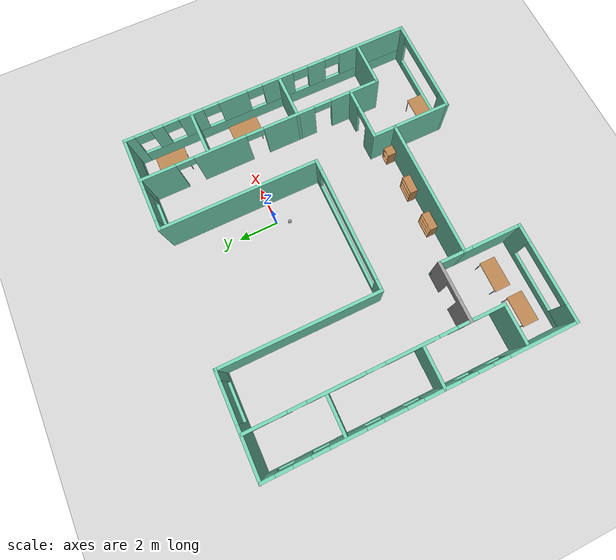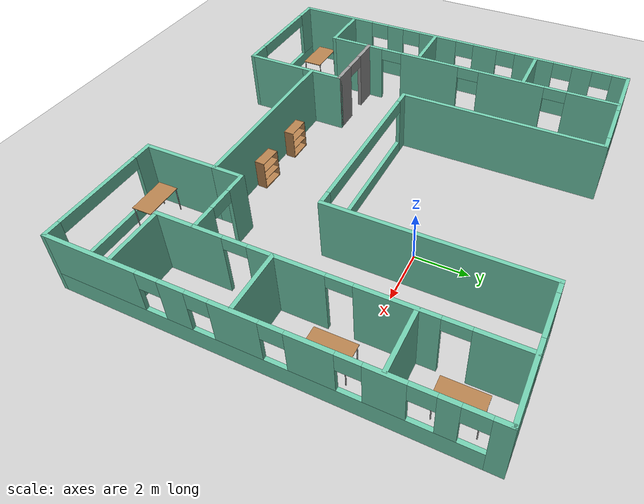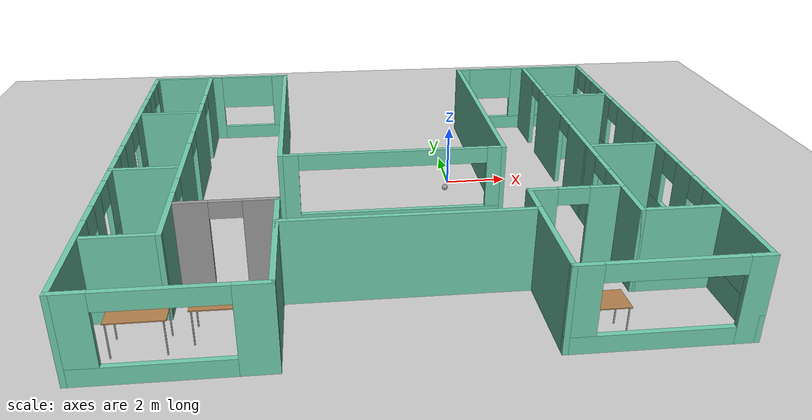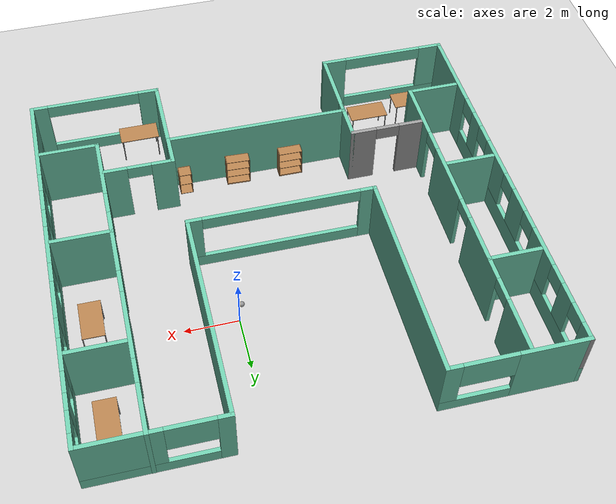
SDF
<sdf version="1.6">
 <world name="default">
  <plugin name="welcome" filename="libwelcome.so"/>
  <light name="sun" type="directional">
   <pose>0 0 10 0 -0 0</pose>
   <diffuse>0.8 0.8 0.8 1</diffuse>
   <specular>0.2 0.2 0.2 1</specular>
   <attenuation>
    <range>1000</range>
    <constant>0.9</constant>
    <linear>0.01</linear>
    <quadratic>0.001</quadratic>
   </attenuation>
   <direction>-0.5 0.1 -0.9</direction>
  </light>
  <model name="ground_plane">
   <static>1</static>
   <link name="link">
    <collision name="collision">
     <geometry><plane><normal>0 0 1</normal><size>100 100</size></plane></geometry>
     <surface>
      <contact><collide_bitmask>65535</collide_bitmask></contact>
      <friction><ode><mu>100</mu><mu2>50</mu2></ode></friction>
     </surface>
    </collision>
    <visual name="visual">
     <cast_shadows>0</cast_shadows>
     <geometry><plane><normal>0 0 1</normal><size>100 100</size></plane></geometry>
     <material>
      <script><uri>file://media/materials/scripts/gazebo.material</uri><name>Gazebo/Grey</name></script>
     </material>
    </visual>
   </link>
  </model>
  <gravity>0 0 -9.8</gravity>
  <magnetic_field>6e-06 2.3e-05 -4.2e-05</magnetic_field>
  <atmosphere type="adiabatic"/>
  <physics name="default_physics" default="0" type="ode">
   <max_step_size>0.001</max_step_size>
   <real_time_factor>1</real_time_factor>
   <real_time_update_rate>1000</real_time_update_rate>
  </physics>
  <scene><ambient>0.4 0.4 0.4 1</ambient><background>0.7 0.7 0.7 1</background><shadows>1</shadows></scene>
  <spherical_coordinates>
   <surface_model>EARTH_WGS84</surface_model>
   <latitude_deg>0</latitude_deg>
   <longitude_deg>0</longitude_deg>
   <elevation>0</elevation>
   <heading_deg>0</heading_deg>
  </spherical_coordinates>
  <model name="building">
   <pose>-2.2336 -2.43171 0 0 -0 0</pose>
   <link name="Wall_0">
    <collision name="Wall_0_Collision">
     <geometry><box><size>0.16 0.15 2.5</size></box></geometry>
     <pose>0 0 1.25 0 -0 0</pose>
    </collision>
    <visual name="Wall_0_Visual">
     <pose>0 0 1.25 0 -0 0</pose>
     <geometry><box><size>0.16 0.15 2.5</size></box></geometry>
     <material>
      <script><uri>file://media/materials/scripts/gazebo.material</uri><name>Gazebo/Grey</name></script>
      <ambient>1 1 1 1</ambient>
     </material>
     <meta><layer>0</layer></meta>
    </visual>
    <pose>-8.275 7.4223 0 0 -0 0</pose>
   </link>
   <link name="Wall_1">
    <pose>-5.845 7.4223 0 0 -0 0</pose>
    <visual name="Wall_1_Visual_0">
     <pose>-1.24921 0 1.25 0 -0 0</pose>
     <geometry><box><size>2.50157 0.15 2.5</size></box></geometry>
     <material>
      <script><uri>file://media/materials/scripts/gazebo.material</uri><name>Gazebo/Grey</name></script>
      <ambient>0.435294 0.796078 0.67451 1</ambient>
     </material>
     <meta><layer>0</layer></meta>
    </visual>
    <collision name="Wall_1_Collision_0">
     <geometry><box><size>2.50157 0.15 2.5</size></box></geometry>
     <pose>-1.24921 0 1.25 0 -0 0</pose>
    </collision>
    <visual name="Wall_1_Visual_1">
     <pose>1.25079 0 0.25 0 -0 0</pose>
     <geometry><box><size>2.49843 0.15 0.5</size></box></geometry>
     <material>
      <script><uri>file://media/materials/scripts/gazebo.material</uri><name>Gazebo/Grey</name></script>
      <ambient>0.435294 0.796078 0.67451 1</ambient>
     </material>
     <meta><layer>0</layer></meta>
    </visual>
    <collision name="Wall_1_Collision_1">
     <geometry><box><size>2.49843 0.15 0.5</size></box></geometry>
     <pose>1.25079 0 0.25 0 -0 0</pose>
    </collision>
    <visual name="Wall_1_Visual_2">
     <pose>2.20141 0 1.5 0 -0 0</pose>
     <geometry><box><size>0.597181 0.15 2</size></box></geometry>
     <material>
      <script><uri>file://media/materials/scripts/gazebo.material</uri><name>Gazebo/Grey</name></script>
      <ambient>0.435294 0.796078 0.67451 1</ambient>
     </material>
     <meta><layer>0</layer></meta>
    </visual>
    <collision name="Wall_1_Collision_2">
     <geometry><box><size>0.597181 0.15 2</size></box></geometry>
     <pose>2.20141 0 1.5 0 -0 0</pose>
    </collision>
    <visual name="Wall_1_Visual_3">
     <pose>0.952195 0 1.9 0 -0 0</pose>
     <geometry><box><size>1.90125 0.15 1.2</size></box></geometry>
     <material>
      <script><uri>file://media/materials/scripts/gazebo.material</uri><name>Gazebo/Grey</name></script>
      <ambient>0.435294 0.796078 0.67451 1</ambient>
     </material>
     <meta><layer>0</layer></meta>
    </visual>
    <collision name="Wall_1_Collision_3">
     <geometry><box><size>1.90125 0.15 1.2</size></box></geometry>
     <pose>0.952195 0 1.9 0 -0 0</pose>
    </collision>
   </link>
   <link name="Wall_10">
    <collision name="Wall_10_Collision">
     <geometry><box><size>3 0.15 2.5</size></box></geometry>
     <pose>0 0 1.25 0 -0 0</pose>
    </collision>
    <visual name="Wall_10_Visual">
     <pose>0 0 1.25 0 -0 0</pose>
     <geometry><box><size>3 0.15 2.5</size></box></geometry>
     <material>
      <script><uri>file://media/materials/scripts/gazebo.material</uri><name>Gazebo/Grey</name></script>
      <ambient>0.435294 0.796078 0.67451 1</ambient>
     </material>
     <meta><layer>0</layer></meta>
    </visual>
    <pose>-3.42 -6.0027 0 0 0 -1.5708</pose>
   </link>
   <link name="Wall_11">
    <pose>-5.845 -7.4277 0 0 -0 3.14159</pose>
    <visual name="Wall_11_Visual_0">
     <pose>-2.0178 0 1.25 0 -0 0</pose>
     <geometry><box><size>0.964396 0.15 2.5</size></box></geometry>
     <material>
      <script><uri>file://media/materials/scripts/gazebo.material</uri><name>Gazebo/Grey</name></script>
      <ambient>0.435294 0.796078 0.67451 1</ambient>
     </material>
     <meta><layer>0</layer></meta>
    </visual>
    <collision name="Wall_11_Collision_0">
     <geometry><box><size>0.964396 0.15 2.5</size></box></geometry>
     <pose>-2.0178 0 1.25 0 -0 0</pose>
    </collision>
    <visual name="Wall_11_Visual_1">
     <pose>0.482198 0 0.25 0 -0 0</pose>
     <geometry><box><size>4.0356 0.15 0.5</size></box></geometry>
     <material>
      <script><uri>file://media/materials/scripts/gazebo.material</uri><name>Gazebo/Grey</name></script>
      <ambient>0.435294 0.796078 0.67451 1</ambient>
     </material>
     <meta><layer>0</layer></meta>
    </visual>
    <collision name="Wall_11_Collision_1">
     <geometry><box><size>4.0356 0.15 0.5</size></box></geometry>
     <pose>0.482198 0 0.25 0 -0 0</pose>
    </collision>
    <visual name="Wall_11_Visual_2">
     <pose>2.0292 0 1.5 0 -0 0</pose>
     <geometry><box><size>0.941604 0.15 2</size></box></geometry>
     <material>
      <script><uri>file://media/materials/scripts/gazebo.material</uri><name>Gazebo/Grey</name></script>
      <ambient>0.435294 0.796078 0.67451 1</ambient>
     </material>
     <meta><layer>0</layer></meta>
    </visual>
    <collision name="Wall_11_Collision_2">
     <geometry><box><size>0.941604 0.15 2</size></box></geometry>
     <pose>2.0292 0 1.5 0 -0 0</pose>
    </collision>
    <visual name="Wall_11_Visual_3">
     <pose>0.011396 0 2.25 0 -0 0</pose>
     <geometry><box><size>3.094 0.15 0.5</size></box></geometry>
     <material>
      <script><uri>file://media/materials/scripts/gazebo.material</uri><name>Gazebo/Grey</name></script>
      <ambient>0.435294 0.796078 0.67451 1</ambient>
     </material>
     <meta><layer>0</layer></meta>
    </visual>
    <collision name="Wall_11_Collision_3">
     <geometry><box><size>3.094 0.15 0.5</size></box></geometry>
     <pose>0.011396 0 2.25 0 -0 0</pose>
    </collision>
   </link>
   <link name="Wall_12">
    <pose>-8.27 -0.002705 0 0 -0 1.5708</pose>
    <visual name="Wall_12_Visual_0">
     <pose>-5.78698 0 1.25 0 -0 0</pose>
     <geometry><box><size>3.42604 0.15 2.5</size></box></geometry>
     <material>
      <script><uri>file://media/materials/scripts/gazebo.material</uri><name>Gazebo/Grey</name></script>
      <ambient>0.435294 0.796078 0.67451 1</ambient>
     </material>
     <meta><layer>0</layer></meta>
    </visual>
    <collision name="Wall_12_Collision_0">
     <geometry><box><size>3.42604 0.15 2.5</size></box></geometry>
     <pose>-5.78698 0 1.25 0 -0 0</pose>
    </collision>
    <visual name="Wall_12_Visual_1">
     <pose>1.71302 0 0.4 0 -0 0</pose>
     <geometry><box><size>11.574 0.15 0.8</size></box></geometry>
     <material>
      <script><uri>file://media/materials/scripts/gazebo.material</uri><name>Gazebo/Grey</name></script>
      <ambient>0.435294 0.796078 0.67451 1</ambient>
     </material>
     <meta><layer>0</layer></meta>
    </visual>
    <collision name="Wall_12_Collision_1">
     <geometry><box><size>11.574 0.15 0.8</size></box></geometry>
     <pose>1.71302 0 0.4 0 -0 0</pose>
    </collision>
    <visual name="Wall_12_Visual_2">
     <pose>-2.89391 0 1.65 0 -0 0</pose>
     <geometry><box><size>0.760102 0.15 1.7</size></box></geometry>
     <material>
      <script><uri>file://media/materials/scripts/gazebo.material</uri><name>Gazebo/Grey</name></script>
      <ambient>0.435294 0.796078 0.67451 1</ambient>
     </material>
     <meta><layer>0</layer></meta>
    </visual>
    <collision name="Wall_12_Collision_2">
     <geometry><box><size>0.760102 0.15 1.7</size></box></geometry>
     <pose>-2.89391 0 1.65 0 -0 0</pose>
    </collision>
    <visual name="Wall_12_Visual_3">
     <pose>-0.844363 0 1.65 0 -0 0</pose>
     <geometry><box><size>1.73899 0.15 1.7</size></box></geometry>
     <material>
      <script><uri>file://media/materials/scripts/gazebo.material</uri><name>Gazebo/Grey</name></script>
      <ambient>0.435294 0.796078 0.67451 1</ambient>
     </material>
     <meta><layer>0</layer></meta>
    </visual>
    <collision name="Wall_12_Collision_3">
     <geometry><box><size>1.73899 0.15 1.7</size></box></geometry>
     <pose>-0.844363 0 1.65 0 -0 0</pose>
    </collision>
    <visual name="Wall_12_Visual_4">
     <pose>1.35813 0 1.65 0 -0 0</pose>
     <geometry><box><size>1.066 0.15 1.7</size></box></geometry>
     <material>
      <script><uri>file://media/materials/scripts/gazebo.material</uri><name>Gazebo/Grey</name></script>
      <ambient>0.435294 0.796078 0.67451 1</ambient>
     </material>
     <meta><layer>0</layer></meta>
    </visual>
    <collision name="Wall_12_Collision_4">
     <geometry><box><size>1.066 0.15 1.7</size></box></geometry>
     <pose>1.35813 0 1.65 0 -0 0</pose>
    </collision>
    <visual name="Wall_12_Visual_5">
     <pose>3.53004 0 1.65 0 -0 0</pose>
     <geometry><box><size>1.67781 0.15 1.7</size></box></geometry>
     <material>
      <script><uri>file://media/materials/scripts/gazebo.material</uri><name>Gazebo/Grey</name></script>
      <ambient>0.435294 0.796078 0.67451 1</ambient>
     </material>
     <meta><layer>0</layer></meta>
    </visual>
    <collision name="Wall_12_Collision_5">
     <geometry><box><size>1.67781 0.15 1.7</size></box></geometry>
     <pose>3.53004 0 1.65 0 -0 0</pose>
    </collision>
    <visual name="Wall_12_Visual_6">
     <pose>5.57958 0 1.65 0 -0 0</pose>
     <geometry><box><size>0.821282 0.15 1.7</size></box></geometry>
     <material>
      <script><uri>file://media/materials/scripts/gazebo.material</uri><name>Gazebo/Grey</name></script>
      <ambient>0.435294 0.796078 0.67451 1</ambient>
     </material>
     <meta><layer>0</layer></meta>
    </visual>
    <collision name="Wall_12_Collision_6">
     <geometry><box><size>0.821282 0.15 1.7</size></box></geometry>
     <pose>5.57958 0 1.65 0 -0 0</pose>
    </collision>
    <visual name="Wall_12_Visual_7">
     <pose>7.14511 0 1.65 0 -0 0</pose>
     <geometry><box><size>0.709774 0.15 1.7</size></box></geometry>
     <material>
      <script><uri>file://media/materials/scripts/gazebo.material</uri><name>Gazebo/Grey</name></script>
      <ambient>0.435294 0.796078 0.67451 1</ambient>
     </material>
     <meta><layer>0</layer></meta>
    </visual>
    <collision name="Wall_12_Collision_7">
     <geometry><box><size>0.709774 0.15 1.7</size></box></geometry>
     <pose>7.14511 0 1.65 0 -0 0</pose>
    </collision>
    <visual name="Wall_12_Visual_8">
     <pose>-3.67396 0 2.15 0 -0 0</pose>
     <geometry><box><size>0.8 0.15 0.7</size></box></geometry>
     <material>
      <script><uri>file://media/materials/scripts/gazebo.material</uri><name>Gazebo/Grey</name></script>
      <ambient>0.435294 0.796078 0.67451 1</ambient>
     </material>
     <meta><layer>0</layer></meta>
    </visual>
    <collision name="Wall_12_Collision_8">
     <geometry><box><size>0.8 0.15 0.7</size></box></geometry>
     <pose>-3.67396 0 2.15 0 -0 0</pose>
    </collision>
    <visual name="Wall_12_Visual_9">
     <pose>-2.11386 0 2.15 0 -0 0</pose>
     <geometry><box><size>0.8 0.15 0.7</size></box></geometry>
     <material>
      <script><uri>file://media/materials/scripts/gazebo.material</uri><name>Gazebo/Grey</name></script>
      <ambient>0.435294 0.796078 0.67451 1</ambient>
     </material>
     <meta><layer>0</layer></meta>
    </visual>
    <collision name="Wall_12_Collision_9">
     <geometry><box><size>0.8 0.15 0.7</size></box></geometry>
     <pose>-2.11386 0 2.15 0 -0 0</pose>
    </collision>
    <visual name="Wall_12_Visual_10">
     <pose>0.425131 0 2.15 0 -0 0</pose>
     <geometry><box><size>0.8 0.15 0.7</size></box></geometry>
     <material>
      <script><uri>file://media/materials/scripts/gazebo.material</uri><name>Gazebo/Grey</name></script>
      <ambient>0.435294 0.796078 0.67451 1</ambient>
     </material>
     <meta><layer>0</layer></meta>
    </visual>
    <collision name="Wall_12_Collision_10">
     <geometry><box><size>0.8 0.15 0.7</size></box></geometry>
     <pose>0.425131 0 2.15 0 -0 0</pose>
    </collision>
    <visual name="Wall_12_Visual_11">
     <pose>2.29114 0 2.15 0 -0 0</pose>
     <geometry><box><size>0.8 0.15 0.7</size></box></geometry>
     <material>
      <script><uri>file://media/materials/scripts/gazebo.material</uri><name>Gazebo/Grey</name></script>
      <ambient>0.435294 0.796078 0.67451 1</ambient>
     </material>
     <meta><layer>0</layer></meta>
    </visual>
    <collision name="Wall_12_Collision_11">
     <geometry><box><size>0.8 0.15 0.7</size></box></geometry>
     <pose>2.29114 0 2.15 0 -0 0</pose>
    </collision>
    <visual name="Wall_12_Visual_12">
     <pose>4.76894 0 2.15 0 -0 0</pose>
     <geometry><box><size>0.8 0.15 0.7</size></box></geometry>
     <material>
      <script><uri>file://media/materials/scripts/gazebo.material</uri><name>Gazebo/Grey</name></script>
      <ambient>0.435294 0.796078 0.67451 1</ambient>
     </material>
     <meta><layer>0</layer></meta>
    </visual>
    <collision name="Wall_12_Collision_12">
     <geometry><box><size>0.8 0.15 0.7</size></box></geometry>
     <pose>4.76894 0 2.15 0 -0 0</pose>
    </collision>
    <visual name="Wall_12_Visual_13">
     <pose>6.39023 0 2.15 0 -0 0</pose>
     <geometry><box><size>0.8 0.15 0.7</size></box></geometry>
     <material>
      <script><uri>file://media/materials/scripts/gazebo.material</uri><name>Gazebo/Grey</name></script>
      <ambient>0.435294 0.796078 0.67451 1</ambient>
     </material>
     <meta><layer>0</layer></meta>
    </visual>
    <collision name="Wall_12_Collision_13">
     <geometry><box><size>0.8 0.15 0.7</size></box></geometry>
     <pose>6.39023 0 2.15 0 -0 0</pose>
    </collision>
   </link>
   <link name="Wall_14">
    <pose>-6.2584 1.1884 0 0 0 -1.5708</pose>
    <visual name="Wall_14_Visual_0">
     <pose>-5.21539 0 1.25 0 -0 0</pose>
     <geometry><box><size>2.06921 0.15 2.5</size></box></geometry>
     <material>
      <script><uri>file://media/materials/scripts/gazebo.material</uri><name>Gazebo/Grey</name></script>
      <ambient>0.435294 0.796078 0.67451 1</ambient>
     </material>
     <meta><layer>0</layer></meta>
    </visual>
    <collision name="Wall_14_Collision_0">
     <geometry><box><size>2.06921 0.15 2.5</size></box></geometry>
     <pose>-5.21539 0 1.25 0 -0 0</pose>
    </collision>
    <visual name="Wall_14_Visual_1">
     <pose>-1.91067 0 1.25 0 -0 0</pose>
     <geometry><box><size>2.74024 0.15 2.5</size></box></geometry>
     <material>
      <script><uri>file://media/materials/scripts/gazebo.material</uri><name>Gazebo/Grey</name></script>
      <ambient>0.435294 0.796078 0.67451 1</ambient>
     </material>
     <meta><layer>0</layer></meta>
    </visual>
    <collision name="Wall_14_Collision_1">
     <geometry><box><size>2.74024 0.15 2.5</size></box></geometry>
     <pose>-1.91067 0 1.25 0 -0 0</pose>
    </collision>
    <visual name="Wall_14_Visual_2">
     <pose>1.65309 0 1.25 0 -0 0</pose>
     <geometry><box><size>2.58729 0.15 2.5</size></box></geometry>
     <material>
      <script><uri>file://media/materials/scripts/gazebo.material</uri><name>Gazebo/Grey</name></script>
      <ambient>0.435294 0.796078 0.67451 1</ambient>
     </material>
     <meta><layer>0</layer></meta>
    </visual>
    <collision name="Wall_14_Collision_2">
     <geometry><box><size>2.58729 0.15 2.5</size></box></geometry>
     <pose>1.65309 0 1.25 0 -0 0</pose>
    </collision>
    <visual name="Wall_14_Visual_3">
     <pose>5.04837 0 1.25 0 -0 0</pose>
     <geometry><box><size>2.40327 0.15 2.5</size></box></geometry>
     <material>
      <script><uri>file://media/materials/scripts/gazebo.material</uri><name>Gazebo/Grey</name></script>
      <ambient>0.435294 0.796078 0.67451 1</ambient>
     </material>
     <meta><layer>0</layer></meta>
    </visual>
    <collision name="Wall_14_Collision_3">
     <geometry><box><size>2.40327 0.15 2.5</size></box></geometry>
     <pose>5.04837 0 1.25 0 -0 0</pose>
    </collision>
    <visual name="Wall_14_Visual_4">
     <pose>-3.73079 0 2.25 0 -0 0</pose>
     <geometry><box><size>0.9 0.15 0.5</size></box></geometry>
     <material>
      <script><uri>file://media/materials/scripts/gazebo.material</uri><name>Gazebo/Grey</name></script>
      <ambient>0.435294 0.796078 0.67451 1</ambient>
     </material>
     <meta><layer>0</layer></meta>
    </visual>
    <collision name="Wall_14_Collision_4">
     <geometry><box><size>0.9 0.15 0.5</size></box></geometry>
     <pose>-3.73079 0 2.25 0 -0 0</pose>
    </collision>
    <visual name="Wall_14_Visual_5">
     <pose>-0.090551 0 2.25 0 -0 0</pose>
     <geometry><box><size>0.9 0.15 0.5</size></box></geometry>
     <material>
      <script><uri>file://media/materials/scripts/gazebo.material</uri><name>Gazebo/Grey</name></script>
      <ambient>0.435294 0.796078 0.67451 1</ambient>
     </material>
     <meta><layer>0</layer></meta>
    </visual>
    <collision name="Wall_14_Collision_5">
     <geometry><box><size>0.9 0.15 0.5</size></box></geometry>
     <pose>-0.090551 0 2.25 0 -0 0</pose>
    </collision>
    <visual name="Wall_14_Visual_6">
     <pose>3.39674 0 2.25 0 -0 0</pose>
     <geometry><box><size>0.9 0.15 0.5</size></box></geometry>
     <material>
      <script><uri>file://media/materials/scripts/gazebo.material</uri><name>Gazebo/Grey</name></script>
      <ambient>0.435294 0.796078 0.67451 1</ambient>
     </material>
     <meta><layer>0</layer></meta>
    </visual>
    <collision name="Wall_14_Collision_6">
     <geometry><box><size>0.9 0.15 0.5</size></box></geometry>
     <pose>3.39674 0 2.25 0 -0 0</pose>
    </collision>
   </link>
   <link name="Wall_15">
    <collision name="Wall_15_Collision">
     <geometry><box><size>2 0.15 2.5</size></box></geometry>
     <pose>0 0 1.25 0 -0 0</pose>
    </collision>
    <visual name="Wall_15_Visual">
     <pose>0 0 1.25 0 -0 0</pose>
     <geometry><box><size>2 0.15 2.5</size></box></geometry>
     <material>
      <script><uri>file://media/materials/scripts/gazebo.material</uri><name>Gazebo/Grey</name></script>
      <ambient>0.435294 0.796078 0.67451 1</ambient>
     </material>
     <meta><layer>0</layer></meta>
    </visual>
    <pose>-7.1834 -4.9866 0 0 -0 3.14159</pose>
   </link>
   <link name="Wall_17">
    <collision name="Wall_17_Collision">
     <geometry><box><size>2 0.15 2.5</size></box></geometry>
     <pose>0 0 1.25 0 -0 0</pose>
    </collision>
    <visual name="Wall_17_Visual">
     <pose>0 0 1.25 0 -0 0</pose>
     <geometry><box><size>2 0.15 2.5</size></box></geometry>
     <material>
      <script><uri>file://media/materials/scripts/gazebo.material</uri><name>Gazebo/Grey</name></script>
      <ambient>0.435294 0.796078 0.67451 1</ambient>
     </material>
     <meta><layer>0</layer></meta>
    </visual>
    <pose>-7.19437 3.60381 0 0 -0 3.14159</pose>
   </link>
   <link name="Wall_2">
    <collision name="Wall_2_Collision">
     <geometry><box><size>8 0.15 2.5</size></box></geometry>
     <pose>0 0 1.25 0 -0 0</pose>
    </collision>
    <visual name="Wall_2_Visual">
     <pose>0 0 1.25 0 -0 0</pose>
     <geometry><box><size>8 0.15 2.5</size></box></geometry>
     <material>
      <script><uri>file://media/materials/scripts/gazebo.material</uri><name>Gazebo/Grey</name></script>
      <ambient>0.435294 0.796078 0.67451 1</ambient>
     </material>
     <meta><layer>0</layer></meta>
    </visual>
    <pose>-3.42 3.49729 0 0 0 -1.5708</pose>
   </link>
   <link name="Wall_21">
    <collision name="Wall_21_Collision">
     <geometry><box><size>2 0.15 2.5</size></box></geometry>
     <pose>0 0 1.25 0 -0 0</pose>
    </collision>
    <visual name="Wall_21_Visual">
     <pose>0 0 1.25 0 -0 0</pose>
     <geometry><box><size>2 0.15 2.5</size></box></geometry>
     <material>
      <script><uri>file://media/materials/scripts/gazebo.material</uri><name>Gazebo/Grey</name></script>
      <ambient>0.435294 0.796078 0.67451 1</ambient>
     </material>
     <meta><layer>0</layer></meta>
    </visual>
    <pose>-7.33273 -0.954134 0 0 -0 0</pose>
   </link>
   <link name="Wall_26">
    <pose>-4.84436 -3.30958 0 0 -0 0</pose>
    <visual name="Wall_26_Visual_0">
     <pose>-0.953335 0 1.25 0 -0 0</pose>
     <geometry><box><size>1.09333 0.15 2.5</size></box></geometry>
     <material>
      <script><uri>file://media/materials/scripts/gazebo.material</uri><name>Gazebo/Grey</name></script>
      <ambient>1 1 1 1</ambient>
     </material>
     <meta><layer>0</layer></meta>
    </visual>
    <collision name="Wall_26_Collision_0">
     <geometry><box><size>1.09333 0.15 2.5</size></box></geometry>
     <pose>-0.953335 0 1.25 0 -0 0</pose>
    </collision>
    <visual name="Wall_26_Visual_1">
     <pose>0.996665 0 1.25 0 -0 0</pose>
     <geometry><box><size>1.00667 0.15 2.5</size></box></geometry>
     <material>
      <script><uri>file://media/materials/scripts/gazebo.material</uri><name>Gazebo/Grey</name></script>
      <ambient>1 1 1 1</ambient>
     </material>
     <meta><layer>0</layer></meta>
    </visual>
    <collision name="Wall_26_Collision_1">
     <geometry><box><size>1.00667 0.15 2.5</size></box></geometry>
     <pose>0.996665 0 1.25 0 -0 0</pose>
    </collision>
    <visual name="Wall_26_Visual_2">
     <pose>0.043331 0 2.25 0 -0 0</pose>
     <geometry><box><size>0.9 0.15 0.5</size></box></geometry>
     <material>
      <script><uri>file://media/materials/scripts/gazebo.material</uri><name>Gazebo/Grey</name></script>
      <ambient>1 1 1 1</ambient>
     </material>
     <meta><layer>0</layer></meta>
    </visual>
    <collision name="Wall_26_Collision_2">
     <geometry><box><size>0.9 0.15 0.5</size></box></geometry>
     <pose>0.043331 0 2.25 0 -0 0</pose>
    </collision>
   </link>
   <link name="Wall_27">
    <collision name="Wall_27_Collision">
     <geometry><box><size>1.75 0.15 2.5</size></box></geometry>
     <pose>0 0 1.25 0 -0 0</pose>
    </collision>
    <visual name="Wall_27_Visual">
     <pose>0 0 1.25 0 -0 0</pose>
     <geometry><box><size>1.75 0.15 2.5</size></box></geometry>
     <material>
      <script><uri>file://media/materials/scripts/gazebo.material</uri><name>Gazebo/Grey</name></script>
      <ambient>0.435294 0.796078 0.67451 1</ambient>
     </material>
     <meta><layer>0</layer></meta>
    </visual>
    <pose>-3.41936 -4.10958 0 0 0 -1.5708</pose>
   </link>
   <link name="Wall_29">
    <pose>6.05856 1.2527 0 0 0 -1.5708</pose>
    <visual name="Wall_29_Visual_0">
     <pose>-5.3209 0 1.25 0 -0 0</pose>
     <geometry><box><size>1.8582 0.15 2.5</size></box></geometry>
     <material>
      <script><uri>file://media/materials/scripts/gazebo.material</uri><name>Gazebo/Grey</name></script>
      <ambient>0.435294 0.796078 0.67451 1</ambient>
     </material>
     <meta><layer>0</layer></meta>
    </visual>
    <collision name="Wall_29_Collision_0">
     <geometry><box><size>1.8582 0.15 2.5</size></box></geometry>
     <pose>-5.3209 0 1.25 0 -0 0</pose>
    </collision>
    <visual name="Wall_29_Visual_1">
     <pose>-2.15227 0 1.25 0 -0 0</pose>
     <geometry><box><size>2.67906 0.15 2.5</size></box></geometry>
     <material>
      <script><uri>file://media/materials/scripts/gazebo.material</uri><name>Gazebo/Grey</name></script>
      <ambient>0.435294 0.796078 0.67451 1</ambient>
     </material>
     <meta><layer>0</layer></meta>
    </visual>
    <collision name="Wall_29_Collision_1">
     <geometry><box><size>2.67906 0.15 2.5</size></box></geometry>
     <pose>-2.15227 0 1.25 0 -0 0</pose>
    </collision>
    <visual name="Wall_29_Visual_2">
     <pose>1.42679 0 1.25 0 -0 0</pose>
     <geometry><box><size>2.67906 0.15 2.5</size></box></geometry>
     <material>
      <script><uri>file://media/materials/scripts/gazebo.material</uri><name>Gazebo/Grey</name></script>
      <ambient>0.435294 0.796078 0.67451 1</ambient>
     </material>
     <meta><layer>0</layer></meta>
    </visual>
    <collision name="Wall_29_Collision_2">
     <geometry><box><size>2.67906 0.15 2.5</size></box></geometry>
     <pose>1.42679 0 1.25 0 -0 0</pose>
    </collision>
    <visual name="Wall_29_Visual_3">
     <pose>4.95816 0 1.25 0 -0 0</pose>
     <geometry><box><size>2.58368 0.15 2.5</size></box></geometry>
     <material>
      <script><uri>file://media/materials/scripts/gazebo.material</uri><name>Gazebo/Grey</name></script>
      <ambient>0.435294 0.796078 0.67451 1</ambient>
     </material>
     <meta><layer>0</layer></meta>
    </visual>
    <collision name="Wall_29_Collision_3">
     <geometry><box><size>2.58368 0.15 2.5</size></box></geometry>
     <pose>4.95816 0 1.25 0 -0 0</pose>
    </collision>
    <visual name="Wall_29_Visual_4">
     <pose>-3.9418 0 2.25 0 -0 0</pose>
     <geometry><box><size>0.9 0.15 0.5</size></box></geometry>
     <material>
      <script><uri>file://media/materials/scripts/gazebo.material</uri><name>Gazebo/Grey</name></script>
      <ambient>0.435294 0.796078 0.67451 1</ambient>
     </material>
     <meta><layer>0</layer></meta>
    </visual>
    <collision name="Wall_29_Collision_4">
     <geometry><box><size>0.9 0.15 0.5</size></box></geometry>
     <pose>-3.9418 0 2.25 0 -0 0</pose>
    </collision>
    <visual name="Wall_29_Visual_5">
     <pose>-0.36274 0 2.25 0 -0 0</pose>
     <geometry><box><size>0.9 0.15 0.5</size></box></geometry>
     <material>
      <script><uri>file://media/materials/scripts/gazebo.material</uri><name>Gazebo/Grey</name></script>
      <ambient>0.435294 0.796078 0.67451 1</ambient>
     </material>
     <meta><layer>0</layer></meta>
    </visual>
    <collision name="Wall_29_Collision_5">
     <geometry><box><size>0.9 0.15 0.5</size></box></geometry>
     <pose>-0.36274 0 2.25 0 -0 0</pose>
    </collision>
    <visual name="Wall_29_Visual_6">
     <pose>3.21632 0 2.25 0 -0 0</pose>
     <geometry><box><size>0.9 0.15 0.5</size></box></geometry>
     <material>
      <script><uri>file://media/materials/scripts/gazebo.material</uri><name>Gazebo/Grey</name></script>
      <ambient>0.435294 0.796078 0.67451 1</ambient>
     </material>
     <meta><layer>0</layer></meta>
    </visual>
    <collision name="Wall_29_Collision_6">
     <geometry><box><size>0.9 0.15 0.5</size></box></geometry>
     <pose>3.21632 0 2.25 0 -0 0</pose>
    </collision>
   </link>
   <link name="Wall_3">
    <pose>0.005 -0.427706 0 0 -0 0</pose>
    <visual name="Wall_3_Visual_0">
     <pose>-3.19054 0 1.25 0 -0 0</pose>
     <geometry><box><size>0.618927 0.15 2.5</size></box></geometry>
     <material>
      <script><uri>file://media/materials/scripts/gazebo.material</uri><name>Gazebo/Grey</name></script>
      <ambient>0.435294 0.796078 0.67451 1</ambient>
     </material>
     <meta><layer>0</layer></meta>
    </visual>
    <collision name="Wall_3_Collision_0">
     <geometry><box><size>0.618927 0.15 2.5</size></box></geometry>
     <pose>-3.19054 0 1.25 0 -0 0</pose>
    </collision>
    <visual name="Wall_3_Visual_1">
     <pose>0.309464 0 0.25 0 -0 0</pose>
     <geometry><box><size>6.38107 0.15 0.5</size></box></geometry>
     <material>
      <script><uri>file://media/materials/scripts/gazebo.material</uri><name>Gazebo/Grey</name></script>
      <ambient>0.435294 0.796078 0.67451 1</ambient>
     </material>
     <meta><layer>0</layer></meta>
    </visual>
    <collision name="Wall_3_Collision_1">
     <geometry><box><size>6.38107 0.15 0.5</size></box></geometry>
     <pose>0.309464 0 0.25 0 -0 0</pose>
    </collision>
    <visual name="Wall_3_Visual_2">
     <pose>3.20246 0 1.5 0 -0 0</pose>
     <geometry><box><size>0.595073 0.15 2</size></box></geometry>
     <material>
      <script><uri>file://media/materials/scripts/gazebo.material</uri><name>Gazebo/Grey</name></script>
      <ambient>0.435294 0.796078 0.67451 1</ambient>
     </material>
     <meta><layer>0</layer></meta>
    </visual>
    <collision name="Wall_3_Collision_2">
     <geometry><box><size>0.595073 0.15 2</size></box></geometry>
     <pose>3.20246 0 1.5 0 -0 0</pose>
    </collision>
    <visual name="Wall_3_Visual_3">
     <pose>0.011927 0 2.25 0 -0 0</pose>
     <geometry><box><size>5.786 0.15 0.5</size></box></geometry>
     <material>
      <script><uri>file://media/materials/scripts/gazebo.material</uri><name>Gazebo/Grey</name></script>
      <ambient>0.435294 0.796078 0.67451 1</ambient>
     </material>
     <meta><layer>0</layer></meta>
    </visual>
    <collision name="Wall_3_Collision_3">
     <geometry><box><size>5.786 0.15 0.5</size></box></geometry>
     <pose>0.011927 0 2.25 0 -0 0</pose>
    </collision>
   </link>
   <link name="Wall_34">
    <collision name="Wall_34_Collision">
     <geometry><box><size>2.25 0.15 2.5</size></box></geometry>
     <pose>0 0 1.25 0 -0 0</pose>
    </collision>
    <visual name="Wall_34_Visual">
     <pose>0 0 1.25 0 -0 0</pose>
     <geometry><box><size>2.25 0.15 2.5</size></box></geometry>
     <material>
      <script><uri>file://media/materials/scripts/gazebo.material</uri><name>Gazebo/Grey</name></script>
      <ambient>0.435294 0.796078 0.67451 1</ambient>
     </material>
     <meta><layer>0</layer></meta>
    </visual>
    <pose>7.13909 4.03207 0 0 -0 0</pose>
   </link>
   <link name="Wall_36">
    <collision name="Wall_36_Collision">
     <geometry><box><size>2.25 0.15 2.5</size></box></geometry>
     <pose>0 0 1.25 0 -0 0</pose>
    </collision>
    <visual name="Wall_36_Visual">
     <pose>0 0 1.25 0 -0 0</pose>
     <geometry><box><size>2.25 0.15 2.5</size></box></geometry>
     <material>
      <script><uri>file://media/materials/scripts/gazebo.material</uri><name>Gazebo/Grey</name></script>
      <ambient>0.435294 0.796078 0.67451 1</ambient>
     </material>
     <meta><layer>0</layer></meta>
    </visual>
    <pose>7.1085 -0.617642 0 0 -0 0</pose>
   </link>
   <link name="Wall_38">
    <collision name="Wall_38_Collision">
     <geometry><box><size>2.25 0.15 2.5</size></box></geometry>
     <pose>0 0 1.25 0 -0 0</pose>
    </collision>
    <visual name="Wall_38_Visual">
     <pose>0 0 1.25 0 -0 0</pose>
     <geometry><box><size>2.25 0.15 2.5</size></box></geometry>
     <material>
      <script><uri>file://media/materials/scripts/gazebo.material</uri><name>Gazebo/Grey</name></script>
      <ambient>0.435294 0.796078 0.67451 1</ambient>
     </material>
     <meta><layer>0</layer></meta>
    </visual>
    <pose>7.10856 -4.9223 0 0 -0 0</pose>
   </link>
   <link name="Wall_4">
    <collision name="Wall_4_Collision">
     <geometry><box><size>8 0.15 2.5</size></box></geometry>
     <pose>0 0 1.25 0 -0 0</pose>
    </collision>
    <visual name="Wall_4_Visual">
     <pose>0 0 1.25 0 -0 0</pose>
     <geometry><box><size>8 0.15 2.5</size></box></geometry>
     <material>
      <script><uri>file://media/materials/scripts/gazebo.material</uri><name>Gazebo/Grey</name></script>
      <ambient>0.435294 0.796078 0.67451 1</ambient>
     </material>
     <meta><layer>0</layer></meta>
    </visual>
    <pose>3.43 3.49729 0 0 -0 1.5708</pose>
   </link>
   <link name="Wall_40">
    <collision name="Wall_40_Collision">
     <geometry><box><size>1.25 0.15 2.5</size></box></geometry>
     <pose>0 0 1.25 0 -0 0</pose>
    </collision>
    <visual name="Wall_40_Visual">
     <pose>0 0 1.25 0 -0 0</pose>
     <geometry><box><size>1.25 0.15 2.5</size></box></geometry>
     <material>
      <script><uri>file://media/materials/scripts/gazebo.material</uri><name>Gazebo/Grey</name></script>
      <ambient>0.435294 0.796078 0.67451 1</ambient>
     </material>
     <meta><layer>0</layer></meta>
    </visual>
    <pose>3.43 -4.02771 0 0 -0 1.5708</pose>
   </link>
   <link name="Wall_41">
    <pose>4.73 -3.4777 0 0 -0 0</pose>
    <visual name="Wall_41_Visual_0">
     <pose>-0.936531 0 1.25 0 -0 0</pose>
     <geometry><box><size>0.876937 0.15 2.5</size></box></geometry>
     <material>
      <script><uri>file://media/materials/scripts/gazebo.material</uri><name>Gazebo/Grey</name></script>
      <ambient>0.435294 0.796078 0.67451 1</ambient>
     </material>
     <meta><layer>0</layer></meta>
    </visual>
    <collision name="Wall_41_Collision_0">
     <geometry><box><size>0.876937 0.15 2.5</size></box></geometry>
     <pose>-0.936531 0 1.25 0 -0 0</pose>
    </collision>
    <visual name="Wall_41_Visual_1">
     <pose>0.888469 0 1.25 0 -0 0</pose>
     <geometry><box><size>0.973063 0.15 2.5</size></box></geometry>
     <material>
      <script><uri>file://media/materials/scripts/gazebo.material</uri><name>Gazebo/Grey</name></script>
      <ambient>0.435294 0.796078 0.67451 1</ambient>
     </material>
     <meta><layer>0</layer></meta>
    </visual>
    <collision name="Wall_41_Collision_1">
     <geometry><box><size>0.973063 0.15 2.5</size></box></geometry>
     <pose>0.888469 0 1.25 0 -0 0</pose>
    </collision>
    <visual name="Wall_41_Visual_2">
     <pose>-0.048063 0 2.25 0 -0 0</pose>
     <geometry><box><size>0.9 0.15 0.5</size></box></geometry>
     <material>
      <script><uri>file://media/materials/scripts/gazebo.material</uri><name>Gazebo/Grey</name></script>
      <ambient>0.435294 0.796078 0.67451 1</ambient>
     </material>
     <meta><layer>0</layer></meta>
    </visual>
    <collision name="Wall_41_Collision_2">
     <geometry><box><size>0.9 0.15 0.5</size></box></geometry>
     <pose>-0.048063 0 2.25 0 -0 0</pose>
    </collision>
   </link>
   <link name="Wall_5">
    <pose>5.855 7.4223 0 0 -0 0</pose>
    <visual name="Wall_5_Visual_0">
     <pose>-2.23537 0 1.25 0 -0 0</pose>
     <geometry><box><size>0.529264 0.15 2.5</size></box></geometry>
     <material>
      <script><uri>file://media/materials/scripts/gazebo.material</uri><name>Gazebo/Grey</name></script>
      <ambient>0.435294 0.796078 0.67451 1</ambient>
     </material>
     <meta><layer>0</layer></meta>
    </visual>
    <collision name="Wall_5_Collision_0">
     <geometry><box><size>0.529264 0.15 2.5</size></box></geometry>
     <pose>-2.23537 0 1.25 0 -0 0</pose>
    </collision>
    <visual name="Wall_5_Visual_1">
     <pose>0.264632 0 0.25 0 -0 0</pose>
     <geometry><box><size>4.47074 0.15 0.5</size></box></geometry>
     <material>
      <script><uri>file://media/materials/scripts/gazebo.material</uri><name>Gazebo/Grey</name></script>
      <ambient>0.435294 0.796078 0.67451 1</ambient>
     </material>
     <meta><layer>0</layer></meta>
    </visual>
    <collision name="Wall_5_Collision_1">
     <geometry><box><size>4.47074 0.15 0.5</size></box></geometry>
     <pose>0.264632 0 0.25 0 -0 0</pose>
    </collision>
    <visual name="Wall_5_Visual_2">
     <pose>1.09289 0 1.5 0 -0 0</pose>
     <geometry><box><size>2.81421 0.15 2</size></box></geometry>
     <material>
      <script><uri>file://media/materials/scripts/gazebo.material</uri><name>Gazebo/Grey</name></script>
      <ambient>0.435294 0.796078 0.67451 1</ambient>
     </material>
     <meta><layer>0</layer></meta>
    </visual>
    <collision name="Wall_5_Collision_2">
     <geometry><box><size>2.81421 0.15 2</size></box></geometry>
     <pose>1.09289 0 1.5 0 -0 0</pose>
    </collision>
    <visual name="Wall_5_Visual_3">
     <pose>-1.14247 0 1.9 0 -0 0</pose>
     <geometry><box><size>1.65653 0.15 1.2</size></box></geometry>
     <material>
      <script><uri>file://media/materials/scripts/gazebo.material</uri><name>Gazebo/Grey</name></script>
      <ambient>0.435294 0.796078 0.67451 1</ambient>
     </material>
     <meta><layer>0</layer></meta>
    </visual>
    <collision name="Wall_5_Collision_3">
     <geometry><box><size>1.65653 0.15 1.2</size></box></geometry>
     <pose>-1.14247 0 1.9 0 -0 0</pose>
    </collision>
   </link>
   <link name="Wall_6">
    <pose>8.28 -0.002705 0 0 0 -1.5708</pose>
    <visual name="Wall_6_Visual_0">
     <pose>-7.20629 0 1.25 0 -0 0</pose>
     <geometry><box><size>0.587413 0.15 2.5</size></box></geometry>
     <material>
      <script><uri>file://media/materials/scripts/gazebo.material</uri><name>Gazebo/Grey</name></script>
      <ambient>0.435294 0.796078 0.67451 1</ambient>
     </material>
     <meta><layer>0</layer></meta>
    </visual>
    <collision name="Wall_6_Collision_0">
     <geometry><box><size>0.587413 0.15 2.5</size></box></geometry>
     <pose>-7.20629 0 1.25 0 -0 0</pose>
    </collision>
    <visual name="Wall_6_Visual_1">
     <pose>0.293707 0 0.4 0 -0 0</pose>
     <geometry><box><size>14.4126 0.15 0.8</size></box></geometry>
     <material>
      <script><uri>file://media/materials/scripts/gazebo.material</uri><name>Gazebo/Grey</name></script>
      <ambient>0.435294 0.796078 0.67451 1</ambient>
     </material>
     <meta><layer>0</layer></meta>
    </visual>
    <collision name="Wall_6_Collision_1">
     <geometry><box><size>14.4126 0.15 0.8</size></box></geometry>
     <pose>0.293707 0 0.4 0 -0 0</pose>
    </collision>
    <visual name="Wall_6_Visual_2">
     <pose>-5.8002 0 1.65 0 -0 0</pose>
     <geometry><box><size>0.624781 0.15 1.7</size></box></geometry>
     <material>
      <script><uri>file://media/materials/scripts/gazebo.material</uri><name>Gazebo/Grey</name></script>
      <ambient>0.435294 0.796078 0.67451 1</ambient>
     </material>
     <meta><layer>0</layer></meta>
    </visual>
    <collision name="Wall_6_Collision_2">
     <geometry><box><size>0.624781 0.15 1.7</size></box></geometry>
     <pose>-5.8002 0 1.65 0 -0 0</pose>
    </collision>
    <visual name="Wall_6_Visual_3">
     <pose>-4.05655 0 1.65 0 -0 0</pose>
     <geometry><box><size>1.2625 0.15 1.7</size></box></geometry>
     <material>
      <script><uri>file://media/materials/scripts/gazebo.material</uri><name>Gazebo/Grey</name></script>
      <ambient>0.435294 0.796078 0.67451 1</ambient>
     </material>
     <meta><layer>0</layer></meta>
    </visual>
    <collision name="Wall_6_Collision_3">
     <geometry><box><size>1.2625 0.15 1.7</size></box></geometry>
     <pose>-4.05655 0 1.65 0 -0 0</pose>
    </collision>
    <visual name="Wall_6_Visual_4">
     <pose>-1.86287 0 1.65 0 -0 0</pose>
     <geometry><box><size>1.52486 0.15 1.7</size></box></geometry>
     <material>
      <script><uri>file://media/materials/scripts/gazebo.material</uri><name>Gazebo/Grey</name></script>
      <ambient>0.435294 0.796078 0.67451 1</ambient>
     </material>
     <meta><layer>0</layer></meta>
    </visual>
    <collision name="Wall_6_Collision_4">
     <geometry><box><size>1.52486 0.15 1.7</size></box></geometry>
     <pose>-1.86287 0 1.65 0 -0 0</pose>
    </collision>
    <visual name="Wall_6_Visual_5">
     <pose>0.523166 0 1.65 0 -0 0</pose>
     <geometry><box><size>1.64722 0.15 1.7</size></box></geometry>
     <material>
      <script><uri>file://media/materials/scripts/gazebo.material</uri><name>Gazebo/Grey</name></script>
      <ambient>0.435294 0.796078 0.67451 1</ambient>
     </material>
     <meta><layer>0</layer></meta>
    </visual>
    <collision name="Wall_6_Collision_5">
     <geometry><box><size>1.64722 0.15 1.7</size></box></geometry>
     <pose>0.523166 0 1.65 0 -0 0</pose>
    </collision>
    <visual name="Wall_6_Visual_6">
     <pose>2.6186 0 1.65 0 -0 0</pose>
     <geometry><box><size>0.943643 0.15 1.7</size></box></geometry>
     <material>
      <script><uri>file://media/materials/scripts/gazebo.material</uri><name>Gazebo/Grey</name></script>
      <ambient>0.435294 0.796078 0.67451 1</ambient>
     </material>
     <meta><layer>0</layer></meta>
    </visual>
    <collision name="Wall_6_Collision_6">
     <geometry><box><size>0.943643 0.15 1.7</size></box></geometry>
     <pose>2.6186 0 1.65 0 -0 0</pose>
    </collision>
    <visual name="Wall_6_Visual_7">
     <pose>5.69521 0 1.65 0 -0 0</pose>
     <geometry><box><size>3.60958 0.15 1.7</size></box></geometry>
     <material>
      <script><uri>file://media/materials/scripts/gazebo.material</uri><name>Gazebo/Grey</name></script>
      <ambient>0.435294 0.796078 0.67451 1</ambient>
     </material>
     <meta><layer>0</layer></meta>
    </visual>
    <collision name="Wall_6_Collision_7">
     <geometry><box><size>3.60958 0.15 1.7</size></box></geometry>
     <pose>5.69521 0 1.65 0 -0 0</pose>
    </collision>
    <visual name="Wall_6_Visual_8">
     <pose>-6.51259 0 2.15 0 -0 0</pose>
     <geometry><box><size>0.8 0.15 0.7</size></box></geometry>
     <material>
      <script><uri>file://media/materials/scripts/gazebo.material</uri><name>Gazebo/Grey</name></script>
      <ambient>0.435294 0.796078 0.67451 1</ambient>
     </material>
     <meta><layer>0</layer></meta>
    </visual>
    <collision name="Wall_6_Collision_8">
     <geometry><box><size>0.8 0.15 0.7</size></box></geometry>
     <pose>-6.51259 0 2.15 0 -0 0</pose>
    </collision>
    <visual name="Wall_6_Visual_9">
     <pose>-5.08781 0 2.15 0 -0 0</pose>
     <geometry><box><size>0.8 0.15 0.7</size></box></geometry>
     <material>
      <script><uri>file://media/materials/scripts/gazebo.material</uri><name>Gazebo/Grey</name></script>
      <ambient>0.435294 0.796078 0.67451 1</ambient>
     </material>
     <meta><layer>0</layer></meta>
    </visual>
    <collision name="Wall_6_Collision_9">
     <geometry><box><size>0.8 0.15 0.7</size></box></geometry>
     <pose>-5.08781 0 2.15 0 -0 0</pose>
    </collision>
    <visual name="Wall_6_Visual_10">
     <pose>-3.0253 0 2.15 0 -0 0</pose>
     <geometry><box><size>0.8 0.15 0.7</size></box></geometry>
     <material>
      <script><uri>file://media/materials/scripts/gazebo.material</uri><name>Gazebo/Grey</name></script>
      <ambient>0.435294 0.796078 0.67451 1</ambient>
     </material>
     <meta><layer>0</layer></meta>
    </visual>
    <collision name="Wall_6_Collision_10">
     <geometry><box><size>0.8 0.15 0.7</size></box></geometry>
     <pose>-3.0253 0 2.15 0 -0 0</pose>
    </collision>
    <visual name="Wall_6_Visual_11">
     <pose>-0.700443 0 2.15 0 -0 0</pose>
     <geometry><box><size>0.8 0.15 0.7</size></box></geometry>
     <material>
      <script><uri>file://media/materials/scripts/gazebo.material</uri><name>Gazebo/Grey</name></script>
      <ambient>0.435294 0.796078 0.67451 1</ambient>
     </material>
     <meta><layer>0</layer></meta>
    </visual>
    <collision name="Wall_6_Collision_11">
     <geometry><box><size>0.8 0.15 0.7</size></box></geometry>
     <pose>-0.700443 0 2.15 0 -0 0</pose>
    </collision>
    <visual name="Wall_6_Visual_12">
     <pose>1.74677 0 2.15 0 -0 0</pose>
     <geometry><box><size>0.8 0.15 0.7</size></box></geometry>
     <material>
      <script><uri>file://media/materials/scripts/gazebo.material</uri><name>Gazebo/Grey</name></script>
      <ambient>0.435294 0.796078 0.67451 1</ambient>
     </material>
     <meta><layer>0</layer></meta>
    </visual>
    <collision name="Wall_6_Collision_12">
     <geometry><box><size>0.8 0.15 0.7</size></box></geometry>
     <pose>1.74677 0 2.15 0 -0 0</pose>
    </collision>
    <visual name="Wall_6_Visual_13">
     <pose>3.49042 0 2.15 0 -0 0</pose>
     <geometry><box><size>0.8 0.15 0.7</size></box></geometry>
     <material>
      <script><uri>file://media/materials/scripts/gazebo.material</uri><name>Gazebo/Grey</name></script>
      <ambient>0.435294 0.796078 0.67451 1</ambient>
     </material>
     <meta><layer>0</layer></meta>
    </visual>
    <collision name="Wall_6_Collision_13">
     <geometry><box><size>0.8 0.15 0.7</size></box></geometry>
     <pose>3.49042 0 2.15 0 -0 0</pose>
    </collision>
   </link>
   <link name="Wall_7">
    <pose>5.855 -7.4277 0 0 -0 3.14159</pose>
    <visual name="Wall_7_Visual_0">
     <pose>-2.16367 0 1.25 0 -0 0</pose>
     <geometry><box><size>0.672659 0.15 2.5</size></box></geometry>
     <material>
      <script><uri>file://media/materials/scripts/gazebo.material</uri><name>Gazebo/Grey</name></script>
      <ambient>0.435294 0.796078 0.67451 1</ambient>
     </material>
     <meta><layer>0</layer></meta>
    </visual>
    <collision name="Wall_7_Collision_0">
     <geometry><box><size>0.672659 0.15 2.5</size></box></geometry>
     <pose>-2.16367 0 1.25 0 -0 0</pose>
    </collision>
    <visual name="Wall_7_Visual_1">
     <pose>0.336329 0 0.25 0 -0 0</pose>
     <geometry><box><size>4.32734 0.15 0.5</size></box></geometry>
     <material>
      <script><uri>file://media/materials/scripts/gazebo.material</uri><name>Gazebo/Grey</name></script>
      <ambient>0.435294 0.796078 0.67451 1</ambient>
     </material>
     <meta><layer>0</layer></meta>
    </visual>
    <collision name="Wall_7_Collision_1">
     <geometry><box><size>4.32734 0.15 0.5</size></box></geometry>
     <pose>0.336329 0 0.25 0 -0 0</pose>
    </collision>
    <visual name="Wall_7_Visual_2">
     <pose>2.09783 0 1.5 0 -0 0</pose>
     <geometry><box><size>0.804341 0.15 2</size></box></geometry>
     <material>
      <script><uri>file://media/materials/scripts/gazebo.material</uri><name>Gazebo/Grey</name></script>
      <ambient>0.435294 0.796078 0.67451 1</ambient>
     </material>
     <meta><layer>0</layer></meta>
    </visual>
    <collision name="Wall_7_Collision_2">
     <geometry><box><size>0.804341 0.15 2</size></box></geometry>
     <pose>2.09783 0 1.5 0 -0 0</pose>
    </collision>
    <visual name="Wall_7_Visual_3">
     <pose>-0.065841 0 2.25 0 -0 0</pose>
     <geometry><box><size>3.523 0.15 0.5</size></box></geometry>
     <material>
      <script><uri>file://media/materials/scripts/gazebo.material</uri><name>Gazebo/Grey</name></script>
      <ambient>0.435294 0.796078 0.67451 1</ambient>
     </material>
     <meta><layer>0</layer></meta>
    </visual>
    <collision name="Wall_7_Collision_3">
     <geometry><box><size>3.523 0.15 0.5</size></box></geometry>
     <pose>-0.065841 0 2.25 0 -0 0</pose>
    </collision>
   </link>
   <link name="Wall_8">
    <collision name="Wall_8_Collision">
     <geometry><box><size>3 0.15 2.5</size></box></geometry>
     <pose>0 0 1.25 0 -0 0</pose>
    </collision>
    <visual name="Wall_8_Visual">
     <pose>0 0 1.25 0 -0 0</pose>
     <geometry><box><size>3 0.15 2.5</size></box></geometry>
     <material>
      <script><uri>file://media/materials/scripts/gazebo.material</uri><name>Gazebo/Grey</name></script>
      <ambient>0.435294 0.796078 0.67451 1</ambient>
     </material>
     <meta><layer>0</layer></meta>
    </visual>
    <pose>3.43 -6.0027 0 0 -0 1.5708</pose>
   </link>
   <link name="Wall_9">
    <collision name="Wall_9_Collision">
     <geometry><box><size>7 0.15 2.5</size></box></geometry>
     <pose>0 0 1.25 0 -0 0</pose>
    </collision>
    <visual name="Wall_9_Visual">
     <pose>0 0 1.25 0 -0 0</pose>
     <geometry><box><size>7 0.15 2.5</size></box></geometry>
     <material>
      <script><uri>file://media/materials/scripts/gazebo.material</uri><name>Gazebo/Grey</name></script>
      <ambient>0.435294 0.796078 0.67451 1</ambient>
     </material>
     <meta><layer>0</layer></meta>
    </visual>
    <pose>0.005 -4.5777 0 0 -0 3.14159</pose>
   </link>
   <static>1</static>
  </model>
  <model name="table">
   <static>1</static>
   <link name="link">
    <collision name="surface">
     <pose>0 0 1 0 -0 0</pose>
     <geometry><box><size>1.5 0.8 0.03</size></box></geometry>
     <surface><friction><ode><mu>0.6</mu><mu2>0.6</mu2></ode></friction></surface>
    </collision>
    <visual name="visual1">
     <pose>0 0 1 0 -0 0</pose>
     <geometry><box><size>1.5 0.8 0.03</size></box></geometry>
     <material>
      <script><uri>file://media/materials/scripts/gazebo.material</uri><name>Gazebo/Wood</name></script>
     </material>
    </visual>
    <collision name="front_left_leg">
     <pose>0.68 0.38 0.5 0 -0 0</pose>
     <geometry><cylinder><radius>0.02</radius><length>1</length></cylinder></geometry>
    </collision>
    <visual name="front_left_leg">
     <pose>0.68 0.38 0.5 0 -0 0</pose>
     <geometry><cylinder><radius>0.02</radius><length>1</length></cylinder></geometry>
     <material>
      <script><uri>file://media/materials/scripts/gazebo.material</uri><name>Gazebo/Grey</name></script>
     </material>
    </visual>
    <collision name="front_right_leg">
     <pose>0.68 -0.38 0.5 0 -0 0</pose>
     <geometry><cylinder><radius>0.02</radius><length>1</length></cylinder></geometry>
    </collision>
    <visual name="front_right_leg">
     <pose>0.68 -0.38 0.5 0 -0 0</pose>
     <geometry><cylinder><radius>0.02</radius><length>1</length></cylinder></geometry>
     <material>
      <script><uri>file://media/materials/scripts/gazebo.material</uri><name>Gazebo/Grey</name></script>
     </material>
    </visual>
    <collision name="back_right_leg">
     <pose>-0.68 -0.38 0.5 0 -0 0</pose>
     <geometry><cylinder><radius>0.02</radius><length>1</length></cylinder></geometry>
    </collision>
    <visual name="back_right_leg">
     <pose>-0.68 -0.38 0.5 0 -0 0</pose>
     <geometry><cylinder><radius>0.02</radius><length>1</length></cylinder></geometry>
     <material>
      <script><uri>file://media/materials/scripts/gazebo.material</uri><name>Gazebo/Grey</name></script>
     </material>
    </visual>
    <collision name="back_left_leg">
     <pose>-0.68 0.38 0.5 0 -0 0</pose>
     <geometry><cylinder><radius>0.02</radius><length>1</length></cylinder></geometry>
    </collision>
    <visual name="back_left_leg">
     <pose>-0.68 0.38 0.5 0 -0 0</pose>
     <geometry><cylinder><radius>0.02</radius><length>1</length></cylinder></geometry>
     <material>
      <script><uri>file://media/materials/scripts/gazebo.material</uri><name>Gazebo/Grey</name></script>
     </material>
    </visual>
   </link>
   <pose>-7.04646 -8.23255 0 0 -0 0</pose>
  </model>
  <model name="table_clone">
   <static>1</static>
   <link name="link">
    <collision name="surface">
     <pose>0 0 1 0 -0 0</pose>
     <geometry><box><size>1.5 0.8 0.03</size></box></geometry>
     <surface><friction><ode><mu>0.6</mu><mu2>0.6</mu2></ode></friction></surface>
    </collision>
    <visual name="visual1">
     <pose>0 0 1 0 -0 0</pose>
     <geometry><box><size>1.5 0.8 0.03</size></box></geometry>
     <material>
      <script><uri>file://media/materials/scripts/gazebo.material</uri><name>Gazebo/Wood</name></script>
     </material>
    </visual>
    <collision name="front_left_leg">
     <pose>0.68 0.38 0.5 0 -0 0</pose>
     <geometry><cylinder><radius>0.02</radius><length>1</length></cylinder></geometry>
    </collision>
    <visual name="front_left_leg">
     <pose>0.68 0.38 0.5 0 -0 0</pose>
     <geometry><cylinder><radius>0.02</radius><length>1</length></cylinder></geometry>
     <material>
      <script><uri>file://media/materials/scripts/gazebo.material</uri><name>Gazebo/Grey</name></script>
     </material>
    </visual>
    <collision name="front_right_leg">
     <pose>0.68 -0.38 0.5 0 -0 0</pose>
     <geometry><cylinder><radius>0.02</radius><length>1</length></cylinder></geometry>
    </collision>
    <visual name="front_right_leg">
     <pose>0.68 -0.38 0.5 0 -0 0</pose>
     <geometry><cylinder><radius>0.02</radius><length>1</length></cylinder></geometry>
     <material>
      <script><uri>file://media/materials/scripts/gazebo.material</uri><name>Gazebo/Grey</name></script>
     </material>
    </visual>
    <collision name="back_right_leg">
     <pose>-0.68 -0.38 0.5 0 -0 0</pose>
     <geometry><cylinder><radius>0.02</radius><length>1</length></cylinder></geometry>
    </collision>
    <visual name="back_right_leg">
     <pose>-0.68 -0.38 0.5 0 -0 0</pose>
     <geometry><cylinder><radius>0.02</radius><length>1</length></cylinder></geometry>
     <material>
      <script><uri>file://media/materials/scripts/gazebo.material</uri><name>Gazebo/Grey</name></script>
     </material>
    </visual>
    <collision name="back_left_leg">
     <pose>-0.68 0.38 0.5 0 -0 0</pose>
     <geometry><cylinder><radius>0.02</radius><length>1</length></cylinder></geometry>
    </collision>
    <visual name="back_left_leg">
     <pose>-0.68 0.38 0.5 0 -0 0</pose>
     <geometry><cylinder><radius>0.02</radius><length>1</length></cylinder></geometry>
     <material>
      <script><uri>file://media/materials/scripts/gazebo.material</uri><name>Gazebo/Grey</name></script>
     </material>
    </visual>
   </link>
   <pose>-9.00293 -8.56346 0 0 -0 0.00672</pose>
  </model>
  <model name="table_clone_2">
   <static>1</static>
   <link name="link">
    <collision name="surface">
     <pose>0 0 1 0 -0 0</pose>
     <geometry><box><size>1.5 0.8 0.03</size></box></geometry>
     <surface><friction><ode><mu>0.6</mu><mu2>0.6</mu2></ode></friction></surface>
    </collision>
    <visual name="visual1">
     <pose>0 0 1 0 -0 0</pose>
     <geometry><box><size>1.5 0.8 0.03</size></box></geometry>
     <material>
      <script><uri>file://media/materials/scripts/gazebo.material</uri><name>Gazebo/Wood</name></script>
     </material>
    </visual>
    <collision name="front_left_leg">
     <pose>0.68 0.38 0.5 0 -0 0</pose>
     <geometry><cylinder><radius>0.02</radius><length>1</length></cylinder></geometry>
    </collision>
    <visual name="front_left_leg">
     <pose>0.68 0.38 0.5 0 -0 0</pose>
     <geometry><cylinder><radius>0.02</radius><length>1</length></cylinder></geometry>
     <material>
      <script><uri>file://media/materials/scripts/gazebo.material</uri><name>Gazebo/Grey</name></script>
     </material>
    </visual>
    <collision name="front_right_leg">
     <pose>0.68 -0.38 0.5 0 -0 0</pose>
     <geometry><cylinder><radius>0.02</radius><length>1</length></cylinder></geometry>
    </collision>
    <visual name="front_right_leg">
     <pose>0.68 -0.38 0.5 0 -0 0</pose>
     <geometry><cylinder><radius>0.02</radius><length>1</length></cylinder></geometry>
     <material>
      <script><uri>file://media/materials/scripts/gazebo.material</uri><name>Gazebo/Grey</name></script>
     </material>
    </visual>
    <collision name="back_right_leg">
     <pose>-0.68 -0.38 0.5 0 -0 0</pose>
     <geometry><cylinder><radius>0.02</radius><length>1</length></cylinder></geometry>
    </collision>
    <visual name="back_right_leg">
     <pose>-0.68 -0.38 0.5 0 -0 0</pose>
     <geometry><cylinder><radius>0.02</radius><length>1</length></cylinder></geometry>
     <material>
      <script><uri>file://media/materials/scripts/gazebo.material</uri><name>Gazebo/Grey</name></script>
     </material>
    </visual>
    <collision name="back_left_leg">
     <pose>-0.68 0.38 0.5 0 -0 0</pose>
     <geometry><cylinder><radius>0.02</radius><length>1</length></cylinder></geometry>
    </collision>
    <visual name="back_left_leg">
     <pose>-0.68 0.38 0.5 0 -0 0</pose>
     <geometry><cylinder><radius>0.02</radius><length>1</length></cylinder></geometry>
     <material>
      <script><uri>file://media/materials/scripts/gazebo.material</uri><name>Gazebo/Grey</name></script>
     </material>
    </visual>
   </link>
   <pose>2.14992 -9.17638 0 0 -0 0.00672</pose>
  </model>
  <model name="table_clone_2_clone">
   <static>1</static>
   <link name="link">
    <collision name="surface">
     <pose>0 0 1 0 -0 0</pose>
     <geometry><box><size>1.5 0.8 0.03</size></box></geometry>
     <surface><friction><ode><mu>0.6</mu><mu2>0.6</mu2></ode></friction></surface>
    </collision>
    <visual name="visual1">
     <pose>0 0 1 0 -0 0</pose>
     <geometry><box><size>1.5 0.8 0.03</size></box></geometry>
     <material>
      <script><uri>file://media/materials/scripts/gazebo.material</uri><name>Gazebo/Wood</name></script>
     </material>
    </visual>
    <collision name="front_left_leg">
     <pose>0.68 0.38 0.5 0 -0 0</pose>
     <geometry><cylinder><radius>0.02</radius><length>1</length></cylinder></geometry>
    </collision>
    <visual name="front_left_leg">
     <pose>0.68 0.38 0.5 0 -0 0</pose>
     <geometry><cylinder><radius>0.02</radius><length>1</length></cylinder></geometry>
     <material>
      <script><uri>file://media/materials/scripts/gazebo.material</uri><name>Gazebo/Grey</name></script>
     </material>
    </visual>
    <collision name="front_right_leg">
     <pose>0.68 -0.38 0.5 0 -0 0</pose>
     <geometry><cylinder><radius>0.02</radius><length>1</length></cylinder></geometry>
    </collision>
    <visual name="front_right_leg">
     <pose>0.68 -0.38 0.5 0 -0 0</pose>
     <geometry><cylinder><radius>0.02</radius><length>1</length></cylinder></geometry>
     <material>
      <script><uri>file://media/materials/scripts/gazebo.material</uri><name>Gazebo/Grey</name></script>
     </material>
    </visual>
    <collision name="back_right_leg">
     <pose>-0.68 -0.38 0.5 0 -0 0</pose>
     <geometry><cylinder><radius>0.02</radius><length>1</length></cylinder></geometry>
    </collision>
    <visual name="back_right_leg">
     <pose>-0.68 -0.38 0.5 0 -0 0</pose>
     <geometry><cylinder><radius>0.02</radius><length>1</length></cylinder></geometry>
     <material>
      <script><uri>file://media/materials/scripts/gazebo.material</uri><name>Gazebo/Grey</name></script>
     </material>
    </visual>
    <collision name="back_left_leg">
     <pose>-0.68 0.38 0.5 0 -0 0</pose>
     <geometry><cylinder><radius>0.02</radius><length>1</length></cylinder></geometry>
    </collision>
    <visual name="back_left_leg">
     <pose>-0.68 0.38 0.5 0 -0 0</pose>
     <geometry><cylinder><radius>0.02</radius><length>1</length></cylinder></geometry>
     <material>
      <script><uri>file://media/materials/scripts/gazebo.material</uri><name>Gazebo/Grey</name></script>
     </material>
    </visual>
   </link>
   <pose>5.03195 -0.555453 0 0 -0 1.56921</pose>
  </model>
  <model name="table_clone_2_clone_0">
   <static>1</static>
   <link name="link">
    <collision name="surface">
     <pose>0 0 1 0 -0 0</pose>
     <geometry><box><size>1.5 0.8 0.03</size></box></geometry>
     <surface><friction><ode><mu>0.6</mu><mu2>0.6</mu2></ode></friction></surface>
    </collision>
    <visual name="visual1">
     <pose>0 0 1 0 -0 0</pose>
     <geometry><box><size>1.5 0.8 0.03</size></box></geometry>
     <material>
      <script><uri>file://media/materials/scripts/gazebo.material</uri><name>Gazebo/Wood</name></script>
     </material>
    </visual>
    <collision name="front_left_leg">
     <pose>0.68 0.38 0.5 0 -0 0</pose>
     <geometry><cylinder><radius>0.02</radius><length>1</length></cylinder></geometry>
    </collision>
    <visual name="front_left_leg">
     <pose>0.68 0.38 0.5 0 -0 0</pose>
     <geometry><cylinder><radius>0.02</radius><length>1</length></cylinder></geometry>
     <material>
      <script><uri>file://media/materials/scripts/gazebo.material</uri><name>Gazebo/Grey</name></script>
     </material>
    </visual>
    <collision name="front_right_leg">
     <pose>0.68 -0.38 0.5 0 -0 0</pose>
     <geometry><cylinder><radius>0.02</radius><length>1</length></cylinder></geometry>
    </collision>
    <visual name="front_right_leg">
     <pose>0.68 -0.38 0.5 0 -0 0</pose>
     <geometry><cylinder><radius>0.02</radius><length>1</length></cylinder></geometry>
     <material>
      <script><uri>file://media/materials/scripts/gazebo.material</uri><name>Gazebo/Grey</name></script>
     </material>
    </visual>
    <collision name="back_right_leg">
     <pose>-0.68 -0.38 0.5 0 -0 0</pose>
     <geometry><cylinder><radius>0.02</radius><length>1</length></cylinder></geometry>
    </collision>
    <visual name="back_right_leg">
     <pose>-0.68 -0.38 0.5 0 -0 0</pose>
     <geometry><cylinder><radius>0.02</radius><length>1</length></cylinder></geometry>
     <material>
      <script><uri>file://media/materials/scripts/gazebo.material</uri><name>Gazebo/Grey</name></script>
     </material>
    </visual>
    <collision name="back_left_leg">
     <pose>-0.68 0.38 0.5 0 -0 0</pose>
     <geometry><cylinder><radius>0.02</radius><length>1</length></cylinder></geometry>
    </collision>
    <visual name="back_left_leg">
     <pose>-0.68 0.38 0.5 0 -0 0</pose>
     <geometry><cylinder><radius>0.02</radius><length>1</length></cylinder></geometry>
     <material>
      <script><uri>file://media/materials/scripts/gazebo.material</uri><name>Gazebo/Grey</name></script>
     </material>
    </visual>
   </link>
   <pose>4.98677 3.39885 0 0 -0 1.56921</pose>
  </model>
  <model name="my_ball">
   <link name="link">
    <inertial>
     <mass>1</mass>
     <inertia><ixx>0.1</ixx><ixy>0</ixy><ixz>0</ixz><iyy>0.1</iyy><iyz>0</iyz><izz>0.1</izz></inertia>
    </inertial>
    <visual name="visual">
     <geometry><sphere><radius>0.1</radius></sphere></geometry>
     <material>
      <script><name>Gazebo/Grey</name><uri>file://media/materials/scripts/gazebo.material</uri></script>
      <shader type="pixel"><normal_map>__default__</normal_map></shader>
      <ambient>1 1 1 1</ambient>
      <diffuse>1 1 1 1</diffuse>
      <specular>1 1 1 1</specular>
      <emissive>1 1 1 1</emissive>
      <lighting>1</lighting>
     </material>
    </visual>
    <collision name="collision">
     <geometry><sphere><radius>0.1</radius></sphere></geometry>
     <surface>
      <friction>
       <ode><mu>1</mu><mu2>1</mu2><fdir1>0 0 0</fdir1><slip1>0</slip1><slip2>0</slip2></ode>
       <torsional>
        <coefficient>1</coefficient>
        <patch_radius>0</patch_radius>
        <surface_radius>0</surface_radius>
        <use_patch_radius>1</use_patch_radius>
        <ode><slip>0</slip></ode>
       </torsional>
      </friction>
      <bounce><restitution_coefficient>0</restitution_coefficient><threshold>1e+06</threshold></bounce>
      <contact>
       <collide_without_contact>0</collide_without_contact>
       <collide_without_contact_bitmask>1</collide_without_contact_bitmask>
       <collide_bitmask>1</collide_bitmask>
       <ode>
        <soft_cfm>0</soft_cfm>
        <soft_erp>0.2</soft_erp>
        <kp>1e+13</kp>
        <kd>1</kd>
        <max_vel>0.01</max_vel>
        <min_depth>0</min_depth>
       </ode>
       <bullet>
        <split_impulse>1</split_impulse>
        <split_impulse_penetration_threshold>-0.01</split_impulse_penetration_threshold>
        <soft_cfm>0</soft_cfm>
        <soft_erp>0.2</soft_erp>
        <kp>1e+13</kp>
        <kd>1</kd>
       </bullet>
      </contact>
     </surface>
    </collision>
   </link>
   <static>0</static>
   <pose>-0.206654 -0.631023 0.1 0 -0 0</pose>
  </model>
  <model name="cabinet">
   <static>1</static>
   <link name="cabinet_bottom_plate">
    <inertial>
     <pose>0 0 -1 0 -0 0</pose>
     <inertia><ixx>2.05</ixx><ixy>0</ixy><ixz>0</ixz><iyy>2.05</iyy><iyz>0</iyz><izz>2.05</izz></inertia>
     <mass>25</mass>
    </inertial>
    <collision name="cabinet_bottom_plate_geom">
     <pose>0 0 0.01 0 -0 0</pose>
     <geometry><box><size>0.45 0.45 0.02</size></box></geometry>
    </collision>
    <visual name="cabinet_bottom_plate_geom_visual">
     <pose>0 0 0.01 0 -0 0</pose>
     <geometry><box><size>0.45 0.45 0.02</size></box></geometry>
     <material>
      <script><uri>file://media/materials/scripts/gazebo.material</uri><name>Gazebo/Wood</name></script>
     </material>
    </visual>
    <collision name="cabinet_bottom_plate_geom_cabinet_back_plate">
     <pose>0.235 0 0.51 0 -0 0</pose>
     <geometry><box><size>0.02 0.45 1.02</size></box></geometry>
    </collision>
    <visual name="cabinet_bottom_plate_geom_cabinet_back_plate_visual">
     <pose>0.235 0 0.51 0 -0 0</pose>
     <geometry><box><size>0.02 0.45 1.02</size></box></geometry>
     <material>
      <script><uri>file://media/materials/scripts/gazebo.material</uri><name>Gazebo/Wood</name></script>
     </material>
    </visual>
    <collision name="cabinet_bottom_plate_geom_cabinet_left_plate">
     <pose>0 0.235 0.51 0 -0 0</pose>
     <geometry><box><size>0.45 0.02 1.02</size></box></geometry>
    </collision>
    <visual name="cabinet_bottom_plate_geom_cabinet_left_plate_visual">
     <pose>0 0.235 0.51 0 -0 0</pose>
     <geometry><box><size>0.45 0.02 1.02</size></box></geometry>
     <material>
      <script><uri>file://media/materials/scripts/gazebo.material</uri><name>Gazebo/Wood</name></script>
     </material>
    </visual>
    <collision name="cabinet_bottom_plate_geom_cabinet_middle_plate">
     <pose>0 0 0.51 0 -0 0</pose>
     <geometry><box><size>0.45 0.45 0.02</size></box></geometry>
    </collision>
    <visual name="cabinet_bottom_plate_geom_cabinet_middle_plate_visual">
     <pose>0 0 0.51 0 -0 0</pose>
     <geometry><box><size>0.45 0.45 0.02</size></box></geometry>
     <material>
      <script><uri>file://media/materials/scripts/gazebo.material</uri><name>Gazebo/Wood</name></script>
     </material>
    </visual>
    <collision name="cabinet_bottom_plate_geom_cabinet_right_plate">
     <pose>0 -0.235 0.51 0 -0 0</pose>
     <geometry><box><size>0.45 0.02 1.02</size></box></geometry>
    </collision>
    <visual name="cabinet_bottom_plate_geom_cabinet_right_plate_visual">
     <pose>0 -0.235 0.51 0 -0 0</pose>
     <geometry><box><size>0.45 0.02 1.02</size></box></geometry>
     <material>
      <script><uri>file://media/materials/scripts/gazebo.material</uri><name>Gazebo/Wood</name></script>
     </material>
    </visual>
    <collision name="cabinet_bottom_plate_geom_cabinet_top_plate">
     <pose>0 0 1.01 0 -0 0</pose>
     <geometry><box><size>0.45 0.45 0.02</size></box></geometry>
    </collision>
    <visual name="cabinet_bottom_plate_geom_cabinet_top_plate_visual">
     <pose>0 0 1.01 0 -0 0</pose>
     <geometry><box><size>0.45 0.45 0.02</size></box></geometry>
     <material>
      <script><uri>file://media/materials/scripts/gazebo.material</uri><name>Gazebo/Wood</name></script>
     </material>
    </visual>
   </link>
   <pose>0.740739 -6.66154 0 0 0 -1.57875</pose>
  </model>
  <model name="bookshelf">
   <static>1</static>
   <link name="link">
    <inertial><mass>1</mass></inertial>
    <collision name="back">
     <pose>0 0.005 0.6 0 -0 0</pose>
     <geometry><box><size>0.9 0.01 1.2</size></box></geometry>
    </collision>
    <visual name="visual1">
     <pose>0 0.005 0.6 0 -0 0</pose>
     <geometry><box><size>0.9 0.01 1.2</size></box></geometry>
     <material>
      <script><uri>file://media/materials/scripts/gazebo.material</uri><name>Gazebo/Wood</name></script>
     </material>
    </visual>
    <collision name="left_side">
     <pose>0.45 -0.195 0.6 0 -0 0</pose>
     <geometry><box><size>0.02 0.4 1.2</size></box></geometry>
    </collision>
    <visual name="visual2">
     <pose>0.45 -0.195 0.6 0 -0 0</pose>
     <geometry><box><size>0.02 0.4 1.2</size></box></geometry>
     <material>
      <script><uri>file://media/materials/scripts/gazebo.material</uri><name>Gazebo/Wood</name></script>
     </material>
    </visual>
    <collision name="right_side">
     <pose>-0.45 -0.195 0.6 0 -0 0</pose>
     <geometry><box><size>0.02 0.4 1.2</size></box></geometry>
    </collision>
    <visual name="visual3">
     <pose>-0.45 -0.195 0.6 0 -0 0</pose>
     <geometry><box><size>0.02 0.4 1.2</size></box></geometry>
     <material>
      <script><uri>file://media/materials/scripts/gazebo.material</uri><name>Gazebo/Wood</name></script>
     </material>
    </visual>
    <collision name="bottom">
     <pose>0 -0.195 0.03 0 -0 0</pose>
     <geometry><box><size>0.88 0.4 0.06</size></box></geometry>
    </collision>
    <visual name="visual4">
     <pose>0 -0.195 0.03 0 -0 0</pose>
     <geometry><box><size>0.88 0.4 0.06</size></box></geometry>
     <material>
      <script><uri>file://media/materials/scripts/gazebo.material</uri><name>Gazebo/Wood</name></script>
     </material>
    </visual>
    <collision name="top">
     <pose>0 -0.195 1.19 0 -0 0</pose>
     <geometry><box><size>0.88 0.4 0.02</size></box></geometry>
    </collision>
    <visual name="visual5">
     <pose>0 -0.195 1.19 0 -0 0</pose>
     <geometry><box><size>0.88 0.4 0.02</size></box></geometry>
     <material>
      <script><uri>file://media/materials/scripts/gazebo.material</uri><name>Gazebo/Wood</name></script>
     </material>
    </visual>
    <collision name="low_shelf">
     <pose>0 -0.195 0.43 0 -0 0</pose>
     <geometry><box><size>0.88 0.4 0.02</size></box></geometry>
    </collision>
    <visual name="visual6">
     <pose>0 -0.195 0.43 0 -0 0</pose>
     <geometry><box><size>0.88 0.4 0.02</size></box></geometry>
     <material>
      <script><uri>file://media/materials/scripts/gazebo.material</uri><name>Gazebo/Wood</name></script>
     </material>
    </visual>
    <collision name="high_shelf">
     <pose>0 -0.195 0.8 0 -0 0</pose>
     <geometry><box><size>0.88 0.4 0.02</size></box></geometry>
    </collision>
    <visual name="visual7">
     <pose>0 -0.195 0.8 0 -0 0</pose>
     <geometry><box><size>0.88 0.4 0.02</size></box></geometry>
     <material>
      <script><uri>file://media/materials/scripts/gazebo.material</uri><name>Gazebo/Wood</name></script>
     </material>
    </visual>
   </link>
   <pose>-1.35704 -6.88426 0 0 -0 3.10501</pose>
  </model>
  <model name="bookshelf_clone">
   <static>1</static>
   <link name="link">
    <inertial><mass>1</mass></inertial>
    <collision name="back">
     <pose>0 0.005 0.6 0 -0 0</pose>
     <geometry><box><size>0.9 0.01 1.2</size></box></geometry>
    </collision>
    <visual name="visual1">
     <pose>0 0.005 0.6 0 -0 0</pose>
     <geometry><box><size>0.9 0.01 1.2</size></box></geometry>
     <material>
      <script><uri>file://media/materials/scripts/gazebo.material</uri><name>Gazebo/Wood</name></script>
     </material>
    </visual>
    <collision name="left_side">
     <pose>0.45 -0.195 0.6 0 -0 0</pose>
     <geometry><box><size>0.02 0.4 1.2</size></box></geometry>
    </collision>
    <visual name="visual2">
     <pose>0.45 -0.195 0.6 0 -0 0</pose>
     <geometry><box><size>0.02 0.4 1.2</size></box></geometry>
     <material>
      <script><uri>file://media/materials/scripts/gazebo.material</uri><name>Gazebo/Wood</name></script>
     </material>
    </visual>
    <collision name="right_side">
     <pose>-0.45 -0.195 0.6 0 -0 0</pose>
     <geometry><box><size>0.02 0.4 1.2</size></box></geometry>
    </collision>
    <visual name="visual3">
     <pose>-0.45 -0.195 0.6 0 -0 0</pose>
     <geometry><box><size>0.02 0.4 1.2</size></box></geometry>
     <material>
      <script><uri>file://media/materials/scripts/gazebo.material</uri><name>Gazebo/Wood</name></script>
     </material>
    </visual>
    <collision name="bottom">
     <pose>0 -0.195 0.03 0 -0 0</pose>
     <geometry><box><size>0.88 0.4 0.06</size></box></geometry>
    </collision>
    <visual name="visual4">
     <pose>0 -0.195 0.03 0 -0 0</pose>
     <geometry><box><size>0.88 0.4 0.06</size></box></geometry>
     <material>
      <script><uri>file://media/materials/scripts/gazebo.material</uri><name>Gazebo/Wood</name></script>
     </material>
    </visual>
    <collision name="top">
     <pose>0 -0.195 1.19 0 -0 0</pose>
     <geometry><box><size>0.88 0.4 0.02</size></box></geometry>
    </collision>
    <visual name="visual5">
     <pose>0 -0.195 1.19 0 -0 0</pose>
     <geometry><box><size>0.88 0.4 0.02</size></box></geometry>
     <material>
      <script><uri>file://media/materials/scripts/gazebo.material</uri><name>Gazebo/Wood</name></script>
     </material>
    </visual>
    <collision name="low_shelf">
     <pose>0 -0.195 0.43 0 -0 0</pose>
     <geometry><box><size>0.88 0.4 0.02</size></box></geometry>
    </collision>
    <visual name="visual6">
     <pose>0 -0.195 0.43 0 -0 0</pose>
     <geometry><box><size>0.88 0.4 0.02</size></box></geometry>
     <material>
      <script><uri>file://media/materials/scripts/gazebo.material</uri><name>Gazebo/Wood</name></script>
     </material>
    </visual>
    <collision name="high_shelf">
     <pose>0 -0.195 0.8 0 -0 0</pose>
     <geometry><box><size>0.88 0.4 0.02</size></box></geometry>
    </collision>
    <visual name="visual7">
     <pose>0 -0.195 0.8 0 -0 0</pose>
     <geometry><box><size>0.88 0.4 0.02</size></box></geometry>
     <material>
      <script><uri>file://media/materials/scripts/gazebo.material</uri><name>Gazebo/Wood</name></script>
     </material>
    </visual>
   </link>
   <pose>-3.43081 -6.85783 0 0 -0 3.13751</pose>
  </model>
 </world>
</sdf>
